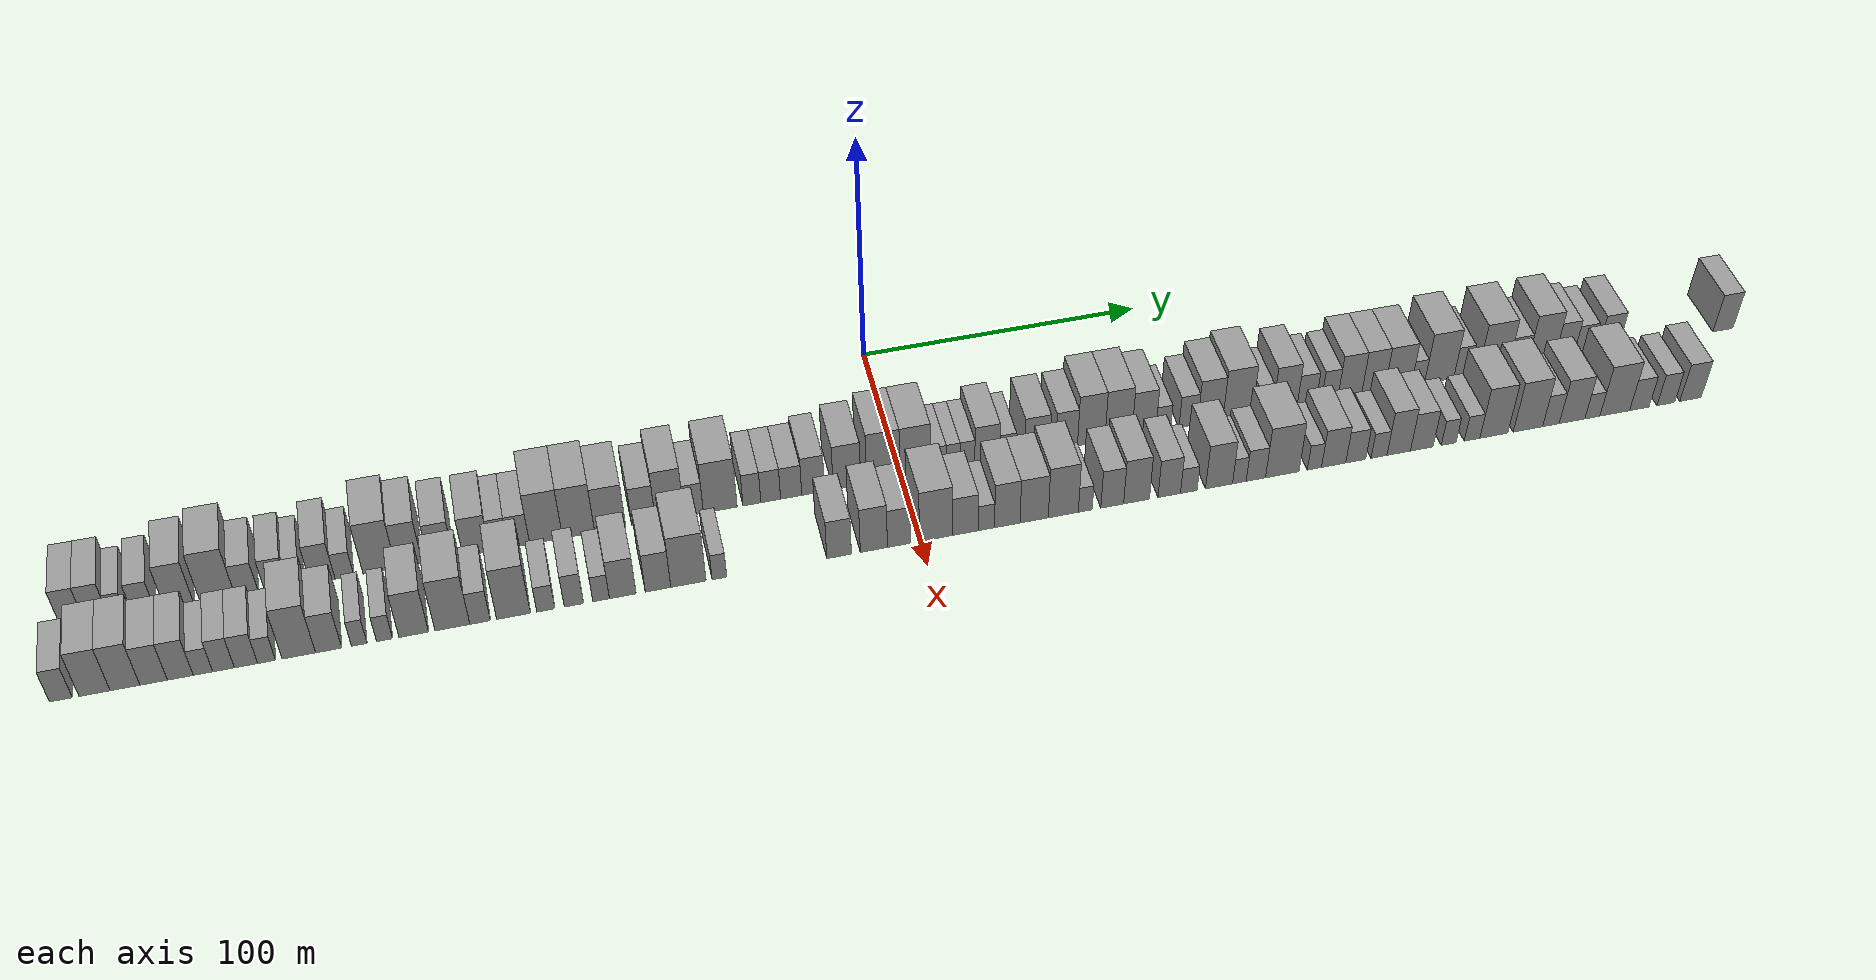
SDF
<sdf version="1.6">
 <world name="default">
  <scene>
   <sky><clouds><speed>12</speed></clouds></sky>
   <ambient>0.4 0.4 0.4 1</ambient>
   <background>0.7 0.7 0.7 1</background>
   <shadows>1</shadows>
  </scene>
  <gravity>0 0 -9.8066</gravity>
  <magnetic_field>6e-06 2.3e-05 -4.2e-05</magnetic_field>
  <physics default="0" name="default_physics" type="ode">
   <ode>
    <solver>
     <type>quick</type>
     <iters>10</iters>
     <sor>1.0</sor>
     <use_dynamic_moi_rescaling>0</use_dynamic_moi_rescaling>
    </solver>
    <constraints>
     <cfm>0</cfm>
     <erp>0.2</erp>
     <contact_max_correcting_vel>100</contact_max_correcting_vel>
     <contact_surface_layer>0.001</contact_surface_layer>
    </constraints>
   </ode>
   <max_step_size>0.004</max_step_size>
   <real_time_factor>1</real_time_factor>
   <real_time_update_rate>250</real_time_update_rate>
  </physics>
  <light name="sun" type="directional">
   <pose>0 0 10 0 0 0</pose>
   <diffuse>0.8 0.8 0.8 1</diffuse>
   <specular>0.2 0.2 0.2 1</specular>
   <attenuation>
    <range>1000</range>
    <constant>0.9</constant>
    <linear>0.01</linear>
    <quadratic>0.001</quadratic>
   </attenuation>
   <direction>-0.5 0.1 -0.9</direction>
  </light>
  <model name="building_1">
   <static>1</static>
   <pose>50.0000 -271.2881 0 0.000000 0.000000 0.000000</pose>
   <link name="link">
    <pose>0 0 9.00 0 0 0</pose>
    <collision name="collision"><geometry><box><size>20.0000 7.4239 18.0000</size></box></geometry></collision>
    <visual name="visual">
     <cast_shadows>0</cast_shadows>
     <geometry><box><size>20.0000 7.4239 18.0000</size></box></geometry>
     <material>
      <script>
       <uri>model://grey_wall/materials/scripts</uri>
       <uri>model://grey_wall/materials/textures</uri>
       <name>vrc/grey_wall</name>
      </script>
     </material>
    </visual>
   </link>
  </model>
  <model name="building_2">
   <static>1</static>
   <pose>50.0000 -263.7839 0 0.000000 0.000000 0.000000</pose>
   <link name="link">
    <pose>0 0 9.00 0 0 0</pose>
    <collision name="collision"><geometry><box><size>20.0000 7.5845 18.0000</size></box></geometry></collision>
    <visual name="visual">
     <cast_shadows>0</cast_shadows>
     <geometry><box><size>20.0000 7.5845 18.0000</size></box></geometry>
     <material>
      <script>
       <uri>model://grey_wall/materials/scripts</uri>
       <uri>model://grey_wall/materials/textures</uri>
       <name>vrc/grey_wall</name>
      </script>
     </material>
    </visual>
   </link>
  </model>
  <model name="building_3">
   <static>1</static>
   <pose>50.0000 -257.3614 0 0.000000 0.000000 0.000000</pose>
   <link name="link">
    <pose>0 0 6.00 0 0 0</pose>
    <collision name="collision"><geometry><box><size>20.0000 5.2606 12.0000</size></box></geometry></collision>
    <visual name="visual">
     <cast_shadows>0</cast_shadows>
     <geometry><box><size>20.0000 5.2606 12.0000</size></box></geometry>
     <material>
      <script>
       <uri>model://grey_wall/materials/scripts</uri>
       <uri>model://grey_wall/materials/textures</uri>
       <name>vrc/grey_wall</name>
      </script>
     </material>
    </visual>
   </link>
  </model>
  <model name="building_4">
   <static>1</static>
   <pose>50.0000 -249.2254 0 0.000000 0.000000 0.000000</pose>
   <link name="link">
    <pose>0 0 7.50 0 0 0</pose>
    <collision name="collision"><geometry><box><size>20.0000 7.0114 15.0000</size></box></geometry></collision>
    <visual name="visual">
     <cast_shadows>0</cast_shadows>
     <geometry><box><size>20.0000 7.0114 15.0000</size></box></geometry>
     <material>
      <script>
       <uri>model://grey_wall/materials/scripts</uri>
       <uri>model://grey_wall/materials/textures</uri>
       <name>vrc/grey_wall</name>
      </script>
     </material>
    </visual>
   </link>
  </model>
  <model name="building_5">
   <static>1</static>
   <pose>50.0000 -238.1553 0 0.000000 0.000000 0.000000</pose>
   <link name="link">
    <pose>0 0 10.50 0 0 0</pose>
    <collision name="collision"><geometry><box><size>20.0000 9.1288 21.0000</size></box></geometry></collision>
    <visual name="visual">
     <cast_shadows>0</cast_shadows>
     <geometry><box><size>20.0000 9.1288 21.0000</size></box></geometry>
     <material>
      <script>
       <uri>model://grey_wall/materials/scripts</uri>
       <uri>model://grey_wall/materials/textures</uri>
       <name>vrc/grey_wall</name>
      </script>
     </material>
    </visual>
   </link>
  </model>
  <model name="building_6">
   <static>1</static>
   <pose>50.0000 -226.0795 0 0.000000 0.000000 0.000000</pose>
   <link name="link">
    <pose>0 0 12.00 0 0 0</pose>
    <collision name="collision"><geometry><box><size>20.0000 11.0227 24.0000</size></box></geometry></collision>
    <visual name="visual">
     <cast_shadows>0</cast_shadows>
     <geometry><box><size>20.0000 11.0227 24.0000</size></box></geometry>
     <material>
      <script>
       <uri>model://grey_wall/materials/scripts</uri>
       <uri>model://grey_wall/materials/textures</uri>
       <name>vrc/grey_wall</name>
      </script>
     </material>
    </visual>
   </link>
  </model>
  <model name="building_7">
   <static>1</static>
   <pose>50.0000 -216.9120 0 0.000000 0.000000 0.000000</pose>
   <link name="link">
    <pose>0 0 7.50 0 0 0</pose>
    <collision name="collision"><geometry><box><size>20.0000 7.3123 15.0000</size></box></geometry></collision>
    <visual name="visual">
     <cast_shadows>0</cast_shadows>
     <geometry><box><size>20.0000 7.3123 15.0000</size></box></geometry>
     <material>
      <script>
       <uri>model://grey_wall/materials/scripts</uri>
       <uri>model://grey_wall/materials/textures</uri>
       <name>vrc/grey_wall</name>
      </script>
     </material>
    </visual>
   </link>
  </model>
  <model name="building_8">
   <static>1</static>
   <pose>50.0000 -207.6067 0 0.000000 0.000000 0.000000</pose>
   <link name="link">
    <pose>0 0 7.50 0 0 0</pose>
    <collision name="collision"><geometry><box><size>20.0000 7.2984 15.0000</size></box></geometry></collision>
    <visual name="visual">
     <cast_shadows>0</cast_shadows>
     <geometry><box><size>20.0000 7.2984 15.0000</size></box></geometry>
     <material>
      <script>
       <uri>model://grey_wall/materials/scripts</uri>
       <uri>model://grey_wall/materials/textures</uri>
       <name>vrc/grey_wall</name>
      </script>
     </material>
    </visual>
   </link>
  </model>
  <model name="building_9">
   <static>1</static>
   <pose>50.0000 -201.3462 0 0.000000 0.000000 0.000000</pose>
   <link name="link">
    <pose>0 0 6.00 0 0 0</pose>
    <collision name="collision"><geometry><box><size>20.0000 5.2227 12.0000</size></box></geometry></collision>
    <visual name="visual">
     <cast_shadows>0</cast_shadows>
     <geometry><box><size>20.0000 5.2227 12.0000</size></box></geometry>
     <material>
      <script>
       <uri>model://grey_wall/materials/scripts</uri>
       <uri>model://grey_wall/materials/textures</uri>
       <name>vrc/grey_wall</name>
      </script>
     </material>
    </visual>
   </link>
  </model>
  <model name="building_10">
   <static>1</static>
   <pose>50.0000 -192.7805 0 0.000000 0.000000 0.000000</pose>
   <link name="link">
    <pose>0 0 9.00 0 0 0</pose>
    <collision name="collision"><geometry><box><size>20.0000 7.9088 18.0000</size></box></geometry></collision>
    <visual name="visual">
     <cast_shadows>0</cast_shadows>
     <geometry><box><size>20.0000 7.9088 18.0000</size></box></geometry>
     <material>
      <script>
       <uri>model://grey_wall/materials/scripts</uri>
       <uri>model://grey_wall/materials/textures</uri>
       <name>vrc/grey_wall</name>
      </script>
     </material>
    </visual>
   </link>
  </model>
  <model name="building_11">
   <static>1</static>
   <pose>50.0000 -185.8272 0 0.000000 0.000000 0.000000</pose>
   <link name="link">
    <pose>0 0 6.00 0 0 0</pose>
    <collision name="collision"><geometry><box><size>20.0000 5.9977 12.0000</size></box></geometry></collision>
    <visual name="visual">
     <cast_shadows>0</cast_shadows>
     <geometry><box><size>20.0000 5.9977 12.0000</size></box></geometry>
     <material>
      <script>
       <uri>model://grey_wall/materials/scripts</uri>
       <uri>model://grey_wall/materials/textures</uri>
       <name>vrc/grey_wall</name>
      </script>
     </material>
    </visual>
   </link>
  </model>
  <model name="building_12">
   <static>1</static>
   <pose>50.0000 -174.4878 0 0.000000 0.000000 0.000000</pose>
   <link name="link">
    <pose>0 0 12.00 0 0 0</pose>
    <collision name="collision"><geometry><box><size>20.0000 10.6813 24.0000</size></box></geometry></collision>
    <visual name="visual">
     <cast_shadows>0</cast_shadows>
     <geometry><box><size>20.0000 10.6813 24.0000</size></box></geometry>
     <material>
      <script>
       <uri>model://grey_wall/materials/scripts</uri>
       <uri>model://grey_wall/materials/textures</uri>
       <name>vrc/grey_wall</name>
      </script>
     </material>
    </visual>
   </link>
  </model>
  <model name="building_13">
   <static>1</static>
   <pose>50.0000 -164.8769 0 0.000000 0.000000 0.000000</pose>
   <link name="link">
    <pose>0 0 10.50 0 0 0</pose>
    <collision name="collision"><geometry><box><size>20.0000 8.5405 21.0000</size></box></geometry></collision>
    <visual name="visual">
     <cast_shadows>0</cast_shadows>
     <geometry><box><size>20.0000 8.5405 21.0000</size></box></geometry>
     <material>
      <script>
       <uri>model://grey_wall/materials/scripts</uri>
       <uri>model://grey_wall/materials/textures</uri>
       <name>vrc/grey_wall</name>
      </script>
     </material>
    </visual>
   </link>
  </model>
  <model name="building_14">
   <static>1</static>
   <pose>50.0000 -154.5401 0 0.000000 0.000000 0.000000</pose>
   <link name="link">
    <pose>0 0 9.00 0 0 0</pose>
    <collision name="collision"><geometry><box><size>20.0000 8.1332 18.0000</size></box></geometry></collision>
    <visual name="visual">
     <cast_shadows>0</cast_shadows>
     <geometry><box><size>20.0000 8.1332 18.0000</size></box></geometry>
     <material>
      <script>
       <uri>model://grey_wall/materials/scripts</uri>
       <uri>model://grey_wall/materials/textures</uri>
       <name>vrc/grey_wall</name>
      </script>
     </material>
    </visual>
   </link>
  </model>
  <model name="building_15">
   <static>1</static>
   <pose>50.0000 -143.0563 0 0.000000 0.000000 0.000000</pose>
   <link name="link">
    <pose>0 0 9.00 0 0 0</pose>
    <collision name="collision"><geometry><box><size>20.0000 8.8343 18.0000</size></box></geometry></collision>
    <visual name="visual">
     <cast_shadows>0</cast_shadows>
     <geometry><box><size>20.0000 8.8343 18.0000</size></box></geometry>
     <material>
      <script>
       <uri>model://grey_wall/materials/scripts</uri>
       <uri>model://grey_wall/materials/textures</uri>
       <name>vrc/grey_wall</name>
      </script>
     </material>
    </visual>
   </link>
  </model>
  <model name="building_16">
   <static>1</static>
   <pose>50.0000 -135.6108 0 0.000000 0.000000 0.000000</pose>
   <link name="link">
    <pose>0 0 7.50 0 0 0</pose>
    <collision name="collision"><geometry><box><size>20.0000 6.0568 15.0000</size></box></geometry></collision>
    <visual name="visual">
     <cast_shadows>0</cast_shadows>
     <geometry><box><size>20.0000 6.0568 15.0000</size></box></geometry>
     <material>
      <script>
       <uri>model://grey_wall/materials/scripts</uri>
       <uri>model://grey_wall/materials/textures</uri>
       <name>vrc/grey_wall</name>
      </script>
     </material>
    </visual>
   </link>
  </model>
  <model name="building_17">
   <static>1</static>
   <pose>50.0000 -129.0847 0 0.000000 0.000000 0.000000</pose>
   <link name="link">
    <pose>0 0 7.50 0 0 0</pose>
    <collision name="collision"><geometry><box><size>20.0000 6.9954 15.0000</size></box></geometry></collision>
    <visual name="visual">
     <cast_shadows>0</cast_shadows>
     <geometry><box><size>20.0000 6.9954 15.0000</size></box></geometry>
     <material>
      <script>
       <uri>model://grey_wall/materials/scripts</uri>
       <uri>model://grey_wall/materials/textures</uri>
       <name>vrc/grey_wall</name>
      </script>
     </material>
    </visual>
   </link>
  </model>
  <model name="building_18">
   <static>1</static>
   <pose>50.0000 -120.1459 0 0.000000 0.000000 0.000000</pose>
   <link name="link">
    <pose>0 0 12.00 0 0 0</pose>
    <collision name="collision"><geometry><box><size>20.0000 10.8822 24.0000</size></box></geometry></collision>
    <visual name="visual">
     <cast_shadows>0</cast_shadows>
     <geometry><box><size>20.0000 10.8822 24.0000</size></box></geometry>
     <material>
      <script>
       <uri>model://grey_wall/materials/scripts</uri>
       <uri>model://grey_wall/materials/textures</uri>
       <name>vrc/grey_wall</name>
      </script>
     </material>
    </visual>
   </link>
  </model>
  <model name="building_19">
   <static>1</static>
   <pose>50.0000 -109.3991 0 0.000000 0.000000 0.000000</pose>
   <link name="link">
    <pose>0 0 12.00 0 0 0</pose>
    <collision name="collision"><geometry><box><size>20.0000 10.6114 24.0000</size></box></geometry></collision>
    <visual name="visual">
     <cast_shadows>0</cast_shadows>
     <geometry><box><size>20.0000 10.6114 24.0000</size></box></geometry>
     <material>
      <script>
       <uri>model://grey_wall/materials/scripts</uri>
       <uri>model://grey_wall/materials/textures</uri>
       <name>vrc/grey_wall</name>
      </script>
     </material>
    </visual>
   </link>
  </model>
  <model name="building_20">
   <static>1</static>
   <pose>50.0000 -98.9195 0 0.000000 0.000000 0.000000</pose>
   <link name="link">
    <pose>0 0 10.50 0 0 0</pose>
    <collision name="collision"><geometry><box><size>20.0000 10.3479 21.0000</size></box></geometry></collision>
    <visual name="visual">
     <cast_shadows>0</cast_shadows>
     <geometry><box><size>20.0000 10.3479 21.0000</size></box></geometry>
     <material>
      <script>
       <uri>model://grey_wall/materials/scripts</uri>
       <uri>model://grey_wall/materials/textures</uri>
       <name>vrc/grey_wall</name>
      </script>
     </material>
    </visual>
   </link>
  </model>
  <model name="building_21">
   <static>1</static>
   <pose>50.0000 -87.7739 0 0.000000 0.000000 0.000000</pose>
   <link name="link">
    <pose>0 0 9.00 0 0 0</pose>
    <collision name="collision"><geometry><box><size>20.0000 7.9433 18.0000</size></box></geometry></collision>
    <visual name="visual">
     <cast_shadows>0</cast_shadows>
     <geometry><box><size>20.0000 7.9433 18.0000</size></box></geometry>
     <material>
      <script>
       <uri>model://grey_wall/materials/scripts</uri>
       <uri>model://grey_wall/materials/textures</uri>
       <name>vrc/grey_wall</name>
      </script>
     </material>
    </visual>
   </link>
  </model>
  <model name="building_22">
   <static>1</static>
   <pose>50.0000 -78.9859 0 0.000000 0.000000 0.000000</pose>
   <link name="link">
    <pose>0 0 12.00 0 0 0</pose>
    <collision name="collision"><geometry><box><size>20.0000 9.6326 24.0000</size></box></geometry></collision>
    <visual name="visual">
     <cast_shadows>0</cast_shadows>
     <geometry><box><size>20.0000 9.6326 24.0000</size></box></geometry>
     <material>
      <script>
       <uri>model://grey_wall/materials/scripts</uri>
       <uri>model://grey_wall/materials/textures</uri>
       <name>vrc/grey_wall</name>
      </script>
     </material>
    </visual>
   </link>
  </model>
  <model name="building_23">
   <static>1</static>
   <pose>50.0000 -70.9266 0 0.000000 0.000000 0.000000</pose>
   <link name="link">
    <pose>0 0 7.50 0 0 0</pose>
    <collision name="collision"><geometry><box><size>20.0000 6.4860 15.0000</size></box></geometry></collision>
    <visual name="visual">
     <cast_shadows>0</cast_shadows>
     <geometry><box><size>20.0000 6.4860 15.0000</size></box></geometry>
     <material>
      <script>
       <uri>model://grey_wall/materials/scripts</uri>
       <uri>model://grey_wall/materials/textures</uri>
       <name>vrc/grey_wall</name>
      </script>
     </material>
    </visual>
   </link>
  </model>
  <model name="building_24">
   <static>1</static>
   <pose>50.0000 -61.9832 0 0.000000 0.000000 0.000000</pose>
   <link name="link">
    <pose>0 0 12.00 0 0 0</pose>
    <collision name="collision"><geometry><box><size>20.0000 11.4007 24.0000</size></box></geometry></collision>
    <visual name="visual">
     <cast_shadows>0</cast_shadows>
     <geometry><box><size>20.0000 11.4007 24.0000</size></box></geometry>
     <material>
      <script>
       <uri>model://grey_wall/materials/scripts</uri>
       <uri>model://grey_wall/materials/textures</uri>
       <name>vrc/grey_wall</name>
      </script>
     </material>
    </visual>
   </link>
  </model>
  <model name="building_25">
   <static>1</static>
   <pose>50.0000 -51.2385 0 0.000000 0.000000 0.000000</pose>
   <link name="link">
    <pose>0 0 7.50 0 0 0</pose>
    <collision name="collision"><geometry><box><size>20.0000 6.0887 15.0000</size></box></geometry></collision>
    <visual name="visual">
     <cast_shadows>0</cast_shadows>
     <geometry><box><size>20.0000 6.0887 15.0000</size></box></geometry>
     <material>
      <script>
       <uri>model://grey_wall/materials/scripts</uri>
       <uri>model://grey_wall/materials/textures</uri>
       <name>vrc/grey_wall</name>
      </script>
     </material>
    </visual>
   </link>
  </model>
  <model name="building_26">
   <static>1</static>
   <pose>50.0000 -44.8371 0 0.000000 0.000000 0.000000</pose>
   <link name="link">
    <pose>0 0 7.50 0 0 0</pose>
    <collision name="collision"><geometry><box><size>20.0000 6.7143 15.0000</size></box></geometry></collision>
    <visual name="visual">
     <cast_shadows>0</cast_shadows>
     <geometry><box><size>20.0000 6.7143 15.0000</size></box></geometry>
     <material>
      <script>
       <uri>model://grey_wall/materials/scripts</uri>
       <uri>model://grey_wall/materials/textures</uri>
       <name>vrc/grey_wall</name>
      </script>
     </material>
    </visual>
   </link>
  </model>
  <model name="building_27">
   <static>1</static>
   <pose>50.0000 -37.8603 0 0.000000 0.000000 0.000000</pose>
   <link name="link">
    <pose>0 0 7.50 0 0 0</pose>
    <collision name="collision"><geometry><box><size>20.0000 7.2393 15.0000</size></box></geometry></collision>
    <visual name="visual">
     <cast_shadows>0</cast_shadows>
     <geometry><box><size>20.0000 7.2393 15.0000</size></box></geometry>
     <material>
      <script>
       <uri>model://grey_wall/materials/scripts</uri>
       <uri>model://grey_wall/materials/textures</uri>
       <name>vrc/grey_wall</name>
      </script>
     </material>
    </visual>
   </link>
  </model>
  <model name="building_28">
   <static>1</static>
   <pose>50.0000 -30.3558 0 0.000000 0.000000 0.000000</pose>
   <link name="link">
    <pose>0 0 9.00 0 0 0</pose>
    <collision name="collision"><geometry><box><size>20.0000 7.7696 18.0000</size></box></geometry></collision>
    <visual name="visual">
     <cast_shadows>0</cast_shadows>
     <geometry><box><size>20.0000 7.7696 18.0000</size></box></geometry>
     <material>
      <script>
       <uri>model://grey_wall/materials/scripts</uri>
       <uri>model://grey_wall/materials/textures</uri>
       <name>vrc/grey_wall</name>
      </script>
     </material>
    </visual>
   </link>
  </model>
  <model name="building_29">
   <static>1</static>
   <pose>50.0000 -18.7199 0 0.000000 0.000000 0.000000</pose>
   <link name="link">
    <pose>0 0 10.50 0 0 0</pose>
    <collision name="collision"><geometry><box><size>20.0000 9.5024 21.0000</size></box></geometry></collision>
    <visual name="visual">
     <cast_shadows>0</cast_shadows>
     <geometry><box><size>20.0000 9.5024 21.0000</size></box></geometry>
     <material>
      <script>
       <uri>model://grey_wall/materials/scripts</uri>
       <uri>model://grey_wall/materials/textures</uri>
       <name>vrc/grey_wall</name>
      </script>
     </material>
    </visual>
   </link>
  </model>
  <model name="building_30">
   <static>1</static>
   <pose>50.0000 -6.2122 0 0.000000 0.000000 0.000000</pose>
   <link name="link">
    <pose>0 0 12.00 0 0 0</pose>
    <collision name="collision"><geometry><box><size>20.0000 11.5130 24.0000</size></box></geometry></collision>
    <visual name="visual">
     <cast_shadows>0</cast_shadows>
     <geometry><box><size>20.0000 11.5130 24.0000</size></box></geometry>
     <material>
      <script>
       <uri>model://grey_wall/materials/scripts</uri>
       <uri>model://grey_wall/materials/textures</uri>
       <name>vrc/grey_wall</name>
      </script>
     </material>
    </visual>
   </link>
  </model>
  <model name="building_31">
   <static>1</static>
   <pose>50.0000 4.8688 0 0.000000 0.000000 0.000000</pose>
   <link name="link">
    <pose>0 0 12.00 0 0 0</pose>
    <collision name="collision"><geometry><box><size>20.0000 10.6490 24.0000</size></box></geometry></collision>
    <visual name="visual">
     <cast_shadows>0</cast_shadows>
     <geometry><box><size>20.0000 10.6490 24.0000</size></box></geometry>
     <material>
      <script>
       <uri>model://grey_wall/materials/scripts</uri>
       <uri>model://grey_wall/materials/textures</uri>
       <name>vrc/grey_wall</name>
      </script>
     </material>
    </visual>
   </link>
  </model>
  <model name="building_32">
   <static>1</static>
   <pose>50.0000 12.9377 0 0.000000 0.000000 0.000000</pose>
   <link name="link">
    <pose>0 0 6.00 0 0 0</pose>
    <collision name="collision"><geometry><box><size>20.0000 5.4888 12.0000</size></box></geometry></collision>
    <visual name="visual">
     <cast_shadows>0</cast_shadows>
     <geometry><box><size>20.0000 5.4888 12.0000</size></box></geometry>
     <material>
      <script>
       <uri>model://grey_wall/materials/scripts</uri>
       <uri>model://grey_wall/materials/textures</uri>
       <name>vrc/grey_wall</name>
      </script>
     </material>
    </visual>
   </link>
  </model>
  <model name="building_33">
   <static>1</static>
   <pose>50.0000 18.0976 0 0.000000 0.000000 0.000000</pose>
   <link name="link">
    <pose>0 0 6.00 0 0 0</pose>
    <collision name="collision"><geometry><box><size>20.0000 4.8309 12.0000</size></box></geometry></collision>
    <visual name="visual">
     <cast_shadows>0</cast_shadows>
     <geometry><box><size>20.0000 4.8309 12.0000</size></box></geometry>
     <material>
      <script>
       <uri>model://grey_wall/materials/scripts</uri>
       <uri>model://grey_wall/materials/textures</uri>
       <name>vrc/grey_wall</name>
      </script>
     </material>
    </visual>
   </link>
  </model>
  <model name="building_34">
   <static>1</static>
   <pose>50.0000 23.0906 0 0.000000 0.000000 0.000000</pose>
   <link name="link">
    <pose>0 0 6.00 0 0 0</pose>
    <collision name="collision"><geometry><box><size>20.0000 5.1552 12.0000</size></box></geometry></collision>
    <visual name="visual">
     <cast_shadows>0</cast_shadows>
     <geometry><box><size>20.0000 5.1552 12.0000</size></box></geometry>
     <material>
      <script>
       <uri>model://grey_wall/materials/scripts</uri>
       <uri>model://grey_wall/materials/textures</uri>
       <name>vrc/grey_wall</name>
      </script>
     </material>
    </visual>
   </link>
  </model>
  <model name="building_35">
   <static>1</static>
   <pose>50.0000 30.0514 0 0.000000 0.000000 0.000000</pose>
   <link name="link">
    <pose>0 0 9.00 0 0 0</pose>
    <collision name="collision"><geometry><box><size>20.0000 8.7663 18.0000</size></box></geometry></collision>
    <visual name="visual">
     <cast_shadows>0</cast_shadows>
     <geometry><box><size>20.0000 8.7663 18.0000</size></box></geometry>
     <material>
      <script>
       <uri>model://grey_wall/materials/scripts</uri>
       <uri>model://grey_wall/materials/textures</uri>
       <name>vrc/grey_wall</name>
      </script>
     </material>
    </visual>
   </link>
  </model>
  <model name="building_36">
   <static>1</static>
   <pose>50.0000 37.3147 0 0.000000 0.000000 0.000000</pose>
   <link name="link">
    <pose>0 0 6.00 0 0 0</pose>
    <collision name="collision"><geometry><box><size>20.0000 5.7603 12.0000</size></box></geometry></collision>
    <visual name="visual">
     <cast_shadows>0</cast_shadows>
     <geometry><box><size>20.0000 5.7603 12.0000</size></box></geometry>
     <material>
      <script>
       <uri>model://grey_wall/materials/scripts</uri>
       <uri>model://grey_wall/materials/textures</uri>
       <name>vrc/grey_wall</name>
      </script>
     </material>
    </visual>
   </link>
  </model>
  <model name="building_37">
   <static>1</static>
   <pose>50.0000 47.6836 0 0.000000 0.000000 0.000000</pose>
   <link name="link">
    <pose>0 0 9.00 0 0 0</pose>
    <collision name="collision"><geometry><box><size>20.0000 8.9776 18.0000</size></box></geometry></collision>
    <visual name="visual">
     <cast_shadows>0</cast_shadows>
     <geometry><box><size>20.0000 8.9776 18.0000</size></box></geometry>
     <material>
      <script>
       <uri>model://grey_wall/materials/scripts</uri>
       <uri>model://grey_wall/materials/textures</uri>
       <name>vrc/grey_wall</name>
      </script>
     </material>
    </visual>
   </link>
  </model>
  <model name="building_38">
   <static>1</static>
   <pose>50.0000 58.0667 0 0.000000 0.000000 0.000000</pose>
   <link name="link">
    <pose>0 0 9.00 0 0 0</pose>
    <collision name="collision"><geometry><box><size>20.0000 7.7886 18.0000</size></box></geometry></collision>
    <visual name="visual">
     <cast_shadows>0</cast_shadows>
     <geometry><box><size>20.0000 7.7886 18.0000</size></box></geometry>
     <material>
      <script>
       <uri>model://grey_wall/materials/scripts</uri>
       <uri>model://grey_wall/materials/textures</uri>
       <name>vrc/grey_wall</name>
      </script>
     </material>
    </visual>
   </link>
  </model>
  <model name="building_39">
   <static>1</static>
   <pose>50.0000 66.8419 0 0.000000 0.000000 0.000000</pose>
   <link name="link">
    <pose>0 0 12.00 0 0 0</pose>
    <collision name="collision"><geometry><box><size>20.0000 9.7617 24.0000</size></box></geometry></collision>
    <visual name="visual">
     <cast_shadows>0</cast_shadows>
     <geometry><box><size>20.0000 9.7617 24.0000</size></box></geometry>
     <material>
      <script>
       <uri>model://grey_wall/materials/scripts</uri>
       <uri>model://grey_wall/materials/textures</uri>
       <name>vrc/grey_wall</name>
      </script>
     </material>
    </visual>
   </link>
  </model>
  <model name="building_40">
   <static>1</static>
   <pose>50.0000 76.5627 0 0.000000 0.000000 0.000000</pose>
   <link name="link">
    <pose>0 0 12.00 0 0 0</pose>
    <collision name="collision"><geometry><box><size>20.0000 9.6800 24.0000</size></box></geometry></collision>
    <visual name="visual">
     <cast_shadows>0</cast_shadows>
     <geometry><box><size>20.0000 9.6800 24.0000</size></box></geometry>
     <material>
      <script>
       <uri>model://grey_wall/materials/scripts</uri>
       <uri>model://grey_wall/materials/textures</uri>
       <name>vrc/grey_wall</name>
      </script>
     </material>
    </visual>
   </link>
  </model>
  <model name="building_41">
   <static>1</static>
   <pose>50.0000 85.6968 0 0.000000 0.000000 0.000000</pose>
   <link name="link">
    <pose>0 0 10.50 0 0 0</pose>
    <collision name="collision"><geometry><box><size>20.0000 8.5882 21.0000</size></box></geometry></collision>
    <visual name="visual">
     <cast_shadows>0</cast_shadows>
     <geometry><box><size>20.0000 8.5882 21.0000</size></box></geometry>
     <material>
      <script>
       <uri>model://grey_wall/materials/scripts</uri>
       <uri>model://grey_wall/materials/textures</uri>
       <name>vrc/grey_wall</name>
      </script>
     </material>
    </visual>
   </link>
  </model>
  <model name="building_42">
   <static>1</static>
   <pose>50.0000 92.6843 0 0.000000 0.000000 0.000000</pose>
   <link name="link">
    <pose>0 0 6.00 0 0 0</pose>
    <collision name="collision"><geometry><box><size>20.0000 5.3866 12.0000</size></box></geometry></collision>
    <visual name="visual">
     <cast_shadows>0</cast_shadows>
     <geometry><box><size>20.0000 5.3866 12.0000</size></box></geometry>
     <material>
      <script>
       <uri>model://grey_wall/materials/scripts</uri>
       <uri>model://grey_wall/materials/textures</uri>
       <name>vrc/grey_wall</name>
      </script>
     </material>
    </visual>
   </link>
  </model>
  <model name="building_43">
   <static>1</static>
   <pose>50.0000 101.7371 0 0.000000 0.000000 0.000000</pose>
   <link name="link">
    <pose>0 0 7.50 0 0 0</pose>
    <collision name="collision"><geometry><box><size>20.0000 6.7191 15.0000</size></box></geometry></collision>
    <visual name="visual">
     <cast_shadows>0</cast_shadows>
     <geometry><box><size>20.0000 6.7191 15.0000</size></box></geometry>
     <material>
      <script>
       <uri>model://grey_wall/materials/scripts</uri>
       <uri>model://grey_wall/materials/textures</uri>
       <name>vrc/grey_wall</name>
      </script>
     </material>
    </visual>
   </link>
  </model>
  <model name="building_44">
   <static>1</static>
   <pose>50.0000 109.6853 0 0.000000 0.000000 0.000000</pose>
   <link name="link">
    <pose>0 0 10.50 0 0 0</pose>
    <collision name="collision"><geometry><box><size>20.0000 9.1772 21.0000</size></box></geometry></collision>
    <visual name="visual">
     <cast_shadows>0</cast_shadows>
     <geometry><box><size>20.0000 9.1772 21.0000</size></box></geometry>
     <material>
      <script>
       <uri>model://grey_wall/materials/scripts</uri>
       <uri>model://grey_wall/materials/textures</uri>
       <name>vrc/grey_wall</name>
      </script>
     </material>
    </visual>
   </link>
  </model>
  <model name="building_45">
   <static>1</static>
   <pose>50.0000 119.6319 0 0.000000 0.000000 0.000000</pose>
   <link name="link">
    <pose>0 0 12.00 0 0 0</pose>
    <collision name="collision"><geometry><box><size>20.0000 10.7161 24.0000</size></box></geometry></collision>
    <visual name="visual">
     <cast_shadows>0</cast_shadows>
     <geometry><box><size>20.0000 10.7161 24.0000</size></box></geometry>
     <material>
      <script>
       <uri>model://grey_wall/materials/scripts</uri>
       <uri>model://grey_wall/materials/textures</uri>
       <name>vrc/grey_wall</name>
      </script>
     </material>
    </visual>
   </link>
  </model>
  <model name="building_46">
   <static>1</static>
   <pose>50.0000 129.7484 0 0.000000 0.000000 0.000000</pose>
   <link name="link">
    <pose>0 0 6.00 0 0 0</pose>
    <collision name="collision"><geometry><box><size>20.0000 5.5169 12.0000</size></box></geometry></collision>
    <visual name="visual">
     <cast_shadows>0</cast_shadows>
     <geometry><box><size>20.0000 5.5169 12.0000</size></box></geometry>
     <material>
      <script>
       <uri>model://grey_wall/materials/scripts</uri>
       <uri>model://grey_wall/materials/textures</uri>
       <name>vrc/grey_wall</name>
      </script>
     </material>
    </visual>
   </link>
  </model>
  <model name="building_47">
   <static>1</static>
   <pose>50.0000 136.9675 0 0.000000 0.000000 0.000000</pose>
   <link name="link">
    <pose>0 0 10.50 0 0 0</pose>
    <collision name="collision"><geometry><box><size>20.0000 8.9213 21.0000</size></box></geometry></collision>
    <visual name="visual">
     <cast_shadows>0</cast_shadows>
     <geometry><box><size>20.0000 8.9213 21.0000</size></box></geometry>
     <material>
      <script>
       <uri>model://grey_wall/materials/scripts</uri>
       <uri>model://grey_wall/materials/textures</uri>
       <name>vrc/grey_wall</name>
      </script>
     </material>
    </visual>
   </link>
  </model>
  <model name="building_48">
   <static>1</static>
   <pose>50.0000 144.8917 0 0.000000 0.000000 0.000000</pose>
   <link name="link">
    <pose>0 0 7.50 0 0 0</pose>
    <collision name="collision"><geometry><box><size>20.0000 6.9271 15.0000</size></box></geometry></collision>
    <visual name="visual">
     <cast_shadows>0</cast_shadows>
     <geometry><box><size>20.0000 6.9271 15.0000</size></box></geometry>
     <material>
      <script>
       <uri>model://grey_wall/materials/scripts</uri>
       <uri>model://grey_wall/materials/textures</uri>
       <name>vrc/grey_wall</name>
      </script>
     </material>
    </visual>
   </link>
  </model>
  <model name="building_49">
   <static>1</static>
   <pose>50.0000 153.3730 0 0.000000 0.000000 0.000000</pose>
   <link name="link">
    <pose>0 0 7.50 0 0 0</pose>
    <collision name="collision"><geometry><box><size>20.0000 6.0354 15.0000</size></box></geometry></collision>
    <visual name="visual">
     <cast_shadows>0</cast_shadows>
     <geometry><box><size>20.0000 6.0354 15.0000</size></box></geometry>
     <material>
      <script>
       <uri>model://grey_wall/materials/scripts</uri>
       <uri>model://grey_wall/materials/textures</uri>
       <name>vrc/grey_wall</name>
      </script>
     </material>
    </visual>
   </link>
  </model>
  <model name="building_50">
   <static>1</static>
   <pose>50.0000 160.8095 0 0.000000 0.000000 0.000000</pose>
   <link name="link">
    <pose>0 0 10.50 0 0 0</pose>
    <collision name="collision"><geometry><box><size>20.0000 8.8377 21.0000</size></box></geometry></collision>
    <visual name="visual">
     <cast_shadows>0</cast_shadows>
     <geometry><box><size>20.0000 8.8377 21.0000</size></box></geometry>
     <material>
      <script>
       <uri>model://grey_wall/materials/scripts</uri>
       <uri>model://grey_wall/materials/textures</uri>
       <name>vrc/grey_wall</name>
      </script>
     </material>
    </visual>
   </link>
  </model>
  <model name="building_51">
   <static>1</static>
   <pose>50.0000 169.5152 0 0.000000 0.000000 0.000000</pose>
   <link name="link">
    <pose>0 0 10.50 0 0 0</pose>
    <collision name="collision"><geometry><box><size>20.0000 8.5737 21.0000</size></box></geometry></collision>
    <visual name="visual">
     <cast_shadows>0</cast_shadows>
     <geometry><box><size>20.0000 8.5737 21.0000</size></box></geometry>
     <material>
      <script>
       <uri>model://grey_wall/materials/scripts</uri>
       <uri>model://grey_wall/materials/textures</uri>
       <name>vrc/grey_wall</name>
      </script>
     </material>
    </visual>
   </link>
  </model>
  <model name="building_52">
   <static>1</static>
   <pose>50.0000 178.7952 0 0.000000 0.000000 0.000000</pose>
   <link name="link">
    <pose>0 0 10.50 0 0 0</pose>
    <collision name="collision"><geometry><box><size>20.0000 9.9862 21.0000</size></box></geometry></collision>
    <visual name="visual">
     <cast_shadows>0</cast_shadows>
     <geometry><box><size>20.0000 9.9862 21.0000</size></box></geometry>
     <material>
      <script>
       <uri>model://grey_wall/materials/scripts</uri>
       <uri>model://grey_wall/materials/textures</uri>
       <name>vrc/grey_wall</name>
      </script>
     </material>
    </visual>
   </link>
  </model>
  <model name="building_53">
   <static>1</static>
   <pose>50.0000 186.2557 0 0.000000 0.000000 0.000000</pose>
   <link name="link">
    <pose>0 0 6.00 0 0 0</pose>
    <collision name="collision"><geometry><box><size>20.0000 4.9349 12.0000</size></box></geometry></collision>
    <visual name="visual">
     <cast_shadows>0</cast_shadows>
     <geometry><box><size>20.0000 4.9349 12.0000</size></box></geometry>
     <material>
      <script>
       <uri>model://grey_wall/materials/scripts</uri>
       <uri>model://grey_wall/materials/textures</uri>
       <name>vrc/grey_wall</name>
      </script>
     </material>
    </visual>
   </link>
  </model>
  <model name="building_54">
   <static>1</static>
   <pose>50.0000 194.2151 0 0.000000 0.000000 0.000000</pose>
   <link name="link">
    <pose>0 0 12.00 0 0 0</pose>
    <collision name="collision"><geometry><box><size>20.0000 10.9838 24.0000</size></box></geometry></collision>
    <visual name="visual">
     <cast_shadows>0</cast_shadows>
     <geometry><box><size>20.0000 10.9838 24.0000</size></box></geometry>
     <material>
      <script>
       <uri>model://grey_wall/materials/scripts</uri>
       <uri>model://grey_wall/materials/textures</uri>
       <name>vrc/grey_wall</name>
      </script>
     </material>
    </visual>
   </link>
  </model>
  <model name="building_55">
   <static>1</static>
   <pose>50.0000 202.7680 0 0.000000 0.000000 0.000000</pose>
   <link name="link">
    <pose>0 0 7.50 0 0 0</pose>
    <collision name="collision"><geometry><box><size>20.0000 6.1220 15.0000</size></box></geometry></collision>
    <visual name="visual">
     <cast_shadows>0</cast_shadows>
     <geometry><box><size>20.0000 6.1220 15.0000</size></box></geometry>
     <material>
      <script>
       <uri>model://grey_wall/materials/scripts</uri>
       <uri>model://grey_wall/materials/textures</uri>
       <name>vrc/grey_wall</name>
      </script>
     </material>
    </visual>
   </link>
  </model>
  <model name="building_56">
   <static>1</static>
   <pose>50.0000 214.5479 0 0.000000 0.000000 0.000000</pose>
   <link name="link">
    <pose>0 0 12.00 0 0 0</pose>
    <collision name="collision"><geometry><box><size>20.0000 11.4379 24.0000</size></box></geometry></collision>
    <visual name="visual">
     <cast_shadows>0</cast_shadows>
     <geometry><box><size>20.0000 11.4379 24.0000</size></box></geometry>
     <material>
      <script>
       <uri>model://grey_wall/materials/scripts</uri>
       <uri>model://grey_wall/materials/textures</uri>
       <name>vrc/grey_wall</name>
      </script>
     </material>
    </visual>
   </link>
  </model>
  <model name="building_57">
   <static>1</static>
   <pose>50.0000 223.8794 0 0.000000 0.000000 0.000000</pose>
   <link name="link">
    <pose>0 0 7.50 0 0 0</pose>
    <collision name="collision"><geometry><box><size>20.0000 7.2250 15.0000</size></box></geometry></collision>
    <visual name="visual">
     <cast_shadows>0</cast_shadows>
     <geometry><box><size>20.0000 7.2250 15.0000</size></box></geometry>
     <material>
      <script>
       <uri>model://grey_wall/materials/scripts</uri>
       <uri>model://grey_wall/materials/textures</uri>
       <name>vrc/grey_wall</name>
      </script>
     </material>
    </visual>
   </link>
  </model>
  <model name="building_58">
   <static>1</static>
   <pose>50.0000 232.6430 0 0.000000 0.000000 0.000000</pose>
   <link name="link">
    <pose>0 0 12.00 0 0 0</pose>
    <collision name="collision"><geometry><box><size>20.0000 10.3021 24.0000</size></box></geometry></collision>
    <visual name="visual">
     <cast_shadows>0</cast_shadows>
     <geometry><box><size>20.0000 10.3021 24.0000</size></box></geometry>
     <material>
      <script>
       <uri>model://grey_wall/materials/scripts</uri>
       <uri>model://grey_wall/materials/textures</uri>
       <name>vrc/grey_wall</name>
      </script>
     </material>
    </visual>
   </link>
  </model>
  <model name="building_59">
   <static>1</static>
   <pose>50.0000 241.4697 0 0.000000 0.000000 0.000000</pose>
   <link name="link">
    <pose>0 0 9.00 0 0 0</pose>
    <collision name="collision"><geometry><box><size>20.0000 7.3514 18.0000</size></box></geometry></collision>
    <visual name="visual">
     <cast_shadows>0</cast_shadows>
     <geometry><box><size>20.0000 7.3514 18.0000</size></box></geometry>
     <material>
      <script>
       <uri>model://grey_wall/materials/scripts</uri>
       <uri>model://grey_wall/materials/textures</uri>
       <name>vrc/grey_wall</name>
      </script>
     </material>
    </visual>
   </link>
  </model>
  <model name="building_60">
   <static>1</static>
   <pose>50.0000 248.7825 0 0.000000 0.000000 0.000000</pose>
   <link name="link">
    <pose>0 0 7.50 0 0 0</pose>
    <collision name="collision"><geometry><box><size>20.0000 7.2742 15.0000</size></box></geometry></collision>
    <visual name="visual">
     <cast_shadows>0</cast_shadows>
     <geometry><box><size>20.0000 7.2742 15.0000</size></box></geometry>
     <material>
      <script>
       <uri>model://grey_wall/materials/scripts</uri>
       <uri>model://grey_wall/materials/textures</uri>
       <name>vrc/grey_wall</name>
      </script>
     </material>
    </visual>
   </link>
  </model>
  <model name="building_61">
   <static>1</static>
   <pose>50.0000 258.3505 0 0.000000 0.000000 0.000000</pose>
   <link name="link">
    <pose>0 0 9.00 0 0 0</pose>
    <collision name="collision"><geometry><box><size>20.0000 7.8619 18.0000</size></box></geometry></collision>
    <visual name="visual">
     <cast_shadows>0</cast_shadows>
     <geometry><box><size>20.0000 7.8619 18.0000</size></box></geometry>
     <material>
      <script>
       <uri>model://grey_wall/materials/scripts</uri>
       <uri>model://grey_wall/materials/textures</uri>
       <name>vrc/grey_wall</name>
      </script>
     </material>
    </visual>
   </link>
  </model>
  <model name="building_62">
   <static>1</static>
   <pose>50.0000 303.1234 0 0.000000 0.000000 0.000000</pose>
   <link name="link">
    <pose>0 0 9.00 0 0 0</pose>
    <collision name="collision"><geometry><box><size>20.0000 7.8946 18.0000</size></box></geometry></collision>
    <visual name="visual">
     <cast_shadows>0</cast_shadows>
     <geometry><box><size>20.0000 7.8946 18.0000</size></box></geometry>
     <material>
      <script>
       <uri>model://grey_wall/materials/scripts</uri>
       <uri>model://grey_wall/materials/textures</uri>
       <name>vrc/grey_wall</name>
      </script>
     </material>
    </visual>
   </link>
  </model>
  <model name="building_63">
   <static>1</static>
   <pose>79.0000 -274.5551 0 0.000000 0.000000 0.000000</pose>
   <link name="link">
    <pose>0 0 7.50 0 0 0</pose>
    <collision name="collision"><geometry><box><size>20.0000 6.8898 15.0000</size></box></geometry></collision>
    <visual name="visual">
     <cast_shadows>0</cast_shadows>
     <geometry><box><size>20.0000 6.8898 15.0000</size></box></geometry>
     <material>
      <script>
       <uri>model://grey_wall/materials/scripts</uri>
       <uri>model://grey_wall/materials/textures</uri>
       <name>vrc/grey_wall</name>
      </script>
     </material>
    </visual>
   </link>
  </model>
  <model name="building_64">
   <static>1</static>
   <pose>79.0000 -264.4121 0 0.000000 0.000000 0.000000</pose>
   <link name="link">
    <pose>0 0 10.50 0 0 0</pose>
    <collision name="collision"><geometry><box><size>20.0000 9.3963 21.0000</size></box></geometry></collision>
    <visual name="visual">
     <cast_shadows>0</cast_shadows>
     <geometry><box><size>20.0000 9.3963 21.0000</size></box></geometry>
     <material>
      <script>
       <uri>model://grey_wall/materials/scripts</uri>
       <uri>model://grey_wall/materials/textures</uri>
       <name>vrc/grey_wall</name>
      </script>
     </material>
    </visual>
   </link>
  </model>
  <model name="building_65">
   <static>1</static>
   <pose>79.0000 -255.1924 0 0.000000 0.000000 0.000000</pose>
   <link name="link">
    <pose>0 0 10.50 0 0 0</pose>
    <collision name="collision"><geometry><box><size>20.0000 9.0431 21.0000</size></box></geometry></collision>
    <visual name="visual">
     <cast_shadows>0</cast_shadows>
     <geometry><box><size>20.0000 9.0431 21.0000</size></box></geometry>
     <material>
      <script>
       <uri>model://grey_wall/materials/scripts</uri>
       <uri>model://grey_wall/materials/textures</uri>
       <name>vrc/grey_wall</name>
      </script>
     </material>
    </visual>
   </link>
  </model>
  <model name="building_66">
   <static>1</static>
   <pose>79.0000 -246.4859 0 0.000000 0.000000 0.000000</pose>
   <link name="link">
    <pose>0 0 9.00 0 0 0</pose>
    <collision name="collision"><geometry><box><size>20.0000 8.3699 18.0000</size></box></geometry></collision>
    <visual name="visual">
     <cast_shadows>0</cast_shadows>
     <geometry><box><size>20.0000 8.3699 18.0000</size></box></geometry>
     <material>
      <script>
       <uri>model://grey_wall/materials/scripts</uri>
       <uri>model://grey_wall/materials/textures</uri>
       <name>vrc/grey_wall</name>
      </script>
     </material>
    </visual>
   </link>
  </model>
  <model name="building_67">
   <static>1</static>
   <pose>79.0000 -238.3547 0 0.000000 0.000000 0.000000</pose>
   <link name="link">
    <pose>0 0 9.00 0 0 0</pose>
    <collision name="collision"><geometry><box><size>20.0000 7.8924 18.0000</size></box></geometry></collision>
    <visual name="visual">
     <cast_shadows>0</cast_shadows>
     <geometry><box><size>20.0000 7.8924 18.0000</size></box></geometry>
     <material>
      <script>
       <uri>model://grey_wall/materials/scripts</uri>
       <uri>model://grey_wall/materials/textures</uri>
       <name>vrc/grey_wall</name>
      </script>
     </material>
    </visual>
   </link>
  </model>
  <model name="building_68">
   <static>1</static>
   <pose>79.0000 -231.4180 0 0.000000 0.000000 0.000000</pose>
   <link name="link">
    <pose>0 0 6.00 0 0 0</pose>
    <collision name="collision"><geometry><box><size>20.0000 5.9810 12.0000</size></box></geometry></collision>
    <visual name="visual">
     <cast_shadows>0</cast_shadows>
     <geometry><box><size>20.0000 5.9810 12.0000</size></box></geometry>
     <material>
      <script>
       <uri>model://grey_wall/materials/scripts</uri>
       <uri>model://grey_wall/materials/textures</uri>
       <name>vrc/grey_wall</name>
      </script>
     </material>
    </visual>
   </link>
  </model>
  <model name="building_69">
   <static>1</static>
   <pose>79.0000 -225.0969 0 0.000000 0.000000 0.000000</pose>
   <link name="link">
    <pose>0 0 7.50 0 0 0</pose>
    <collision name="collision"><geometry><box><size>20.0000 6.6612 15.0000</size></box></geometry></collision>
    <visual name="visual">
     <cast_shadows>0</cast_shadows>
     <geometry><box><size>20.0000 6.6612 15.0000</size></box></geometry>
     <material>
      <script>
       <uri>model://grey_wall/materials/scripts</uri>
       <uri>model://grey_wall/materials/textures</uri>
       <name>vrc/grey_wall</name>
      </script>
     </material>
    </visual>
   </link>
  </model>
  <model name="building_70">
   <static>1</static>
   <pose>79.0000 -218.1759 0 0.000000 0.000000 0.000000</pose>
   <link name="link">
    <pose>0 0 7.50 0 0 0</pose>
    <collision name="collision"><geometry><box><size>20.0000 7.1807 15.0000</size></box></geometry></collision>
    <visual name="visual">
     <cast_shadows>0</cast_shadows>
     <geometry><box><size>20.0000 7.1807 15.0000</size></box></geometry>
     <material>
      <script>
       <uri>model://grey_wall/materials/scripts</uri>
       <uri>model://grey_wall/materials/textures</uri>
       <name>vrc/grey_wall</name>
      </script>
     </material>
    </visual>
   </link>
  </model>
  <model name="building_71">
   <static>1</static>
   <pose>79.0000 -211.8212 0 0.000000 0.000000 0.000000</pose>
   <link name="link">
    <pose>0 0 6.00 0 0 0</pose>
    <collision name="collision"><geometry><box><size>20.0000 5.5285 12.0000</size></box></geometry></collision>
    <visual name="visual">
     <cast_shadows>0</cast_shadows>
     <geometry><box><size>20.0000 5.5285 12.0000</size></box></geometry>
     <material>
      <script>
       <uri>model://grey_wall/materials/scripts</uri>
       <uri>model://grey_wall/materials/textures</uri>
       <name>vrc/grey_wall</name>
      </script>
     </material>
    </visual>
   </link>
  </model>
  <model name="building_72">
   <static>1</static>
   <pose>79.0000 -201.8440 0 0.000000 0.000000 0.000000</pose>
   <link name="link">
    <pose>0 0 12.00 0 0 0</pose>
    <collision name="collision"><geometry><box><size>20.0000 10.4260 24.0000</size></box></geometry></collision>
    <visual name="visual">
     <cast_shadows>0</cast_shadows>
     <geometry><box><size>20.0000 10.4260 24.0000</size></box></geometry>
     <material>
      <script>
       <uri>model://grey_wall/materials/scripts</uri>
       <uri>model://grey_wall/materials/textures</uri>
       <name>vrc/grey_wall</name>
      </script>
     </material>
    </visual>
   </link>
  </model>
  <model name="building_73">
   <static>1</static>
   <pose>79.0000 -192.5272 0 0.000000 0.000000 0.000000</pose>
   <link name="link">
    <pose>0 0 9.00 0 0 0</pose>
    <collision name="collision"><geometry><box><size>20.0000 8.2077 18.0000</size></box></geometry></collision>
    <visual name="visual">
     <cast_shadows>0</cast_shadows>
     <geometry><box><size>20.0000 8.2077 18.0000</size></box></geometry>
     <material>
      <script>
       <uri>model://grey_wall/materials/scripts</uri>
       <uri>model://grey_wall/materials/textures</uri>
       <name>vrc/grey_wall</name>
      </script>
     </material>
    </visual>
   </link>
  </model>
  <model name="building_74">
   <static>1</static>
   <pose>79.0000 -182.9778 0 0.000000 0.000000 0.000000</pose>
   <link name="link">
    <pose>0 0 6.00 0 0 0</pose>
    <collision name="collision"><geometry><box><size>20.0000 4.8911 12.0000</size></box></geometry></collision>
    <visual name="visual">
     <cast_shadows>0</cast_shadows>
     <geometry><box><size>20.0000 4.8911 12.0000</size></box></geometry>
     <material>
      <script>
       <uri>model://grey_wall/materials/scripts</uri>
       <uri>model://grey_wall/materials/textures</uri>
       <name>vrc/grey_wall</name>
      </script>
     </material>
    </visual>
   </link>
  </model>
  <model name="building_75">
   <static>1</static>
   <pose>79.0000 -175.0180 0 0.000000 0.000000 0.000000</pose>
   <link name="link">
    <pose>0 0 6.00 0 0 0</pose>
    <collision name="collision"><geometry><box><size>20.0000 5.0286 12.0000</size></box></geometry></collision>
    <visual name="visual">
     <cast_shadows>0</cast_shadows>
     <geometry><box><size>20.0000 5.0286 12.0000</size></box></geometry>
     <material>
      <script>
       <uri>model://grey_wall/materials/scripts</uri>
       <uri>model://grey_wall/materials/textures</uri>
       <name>vrc/grey_wall</name>
      </script>
     </material>
    </visual>
   </link>
  </model>
  <model name="building_76">
   <static>1</static>
   <pose>79.0000 -165.8195 0 0.000000 0.000000 0.000000</pose>
   <link name="link">
    <pose>0 0 10.50 0 0 0</pose>
    <collision name="collision"><geometry><box><size>20.0000 9.3684 21.0000</size></box></geometry></collision>
    <visual name="visual">
     <cast_shadows>0</cast_shadows>
     <geometry><box><size>20.0000 9.3684 21.0000</size></box></geometry>
     <material>
      <script>
       <uri>model://grey_wall/materials/scripts</uri>
       <uri>model://grey_wall/materials/textures</uri>
       <name>vrc/grey_wall</name>
      </script>
     </material>
    </visual>
   </link>
  </model>
  <model name="building_77">
   <static>1</static>
   <pose>79.0000 -153.5927 0 0.000000 0.000000 0.000000</pose>
   <link name="link">
    <pose>0 0 12.00 0 0 0</pose>
    <collision name="collision"><geometry><box><size>20.0000 11.0852 24.0000</size></box></geometry></collision>
    <visual name="visual">
     <cast_shadows>0</cast_shadows>
     <geometry><box><size>20.0000 11.0852 24.0000</size></box></geometry>
     <material>
      <script>
       <uri>model://grey_wall/materials/scripts</uri>
       <uri>model://grey_wall/materials/textures</uri>
       <name>vrc/grey_wall</name>
      </script>
     </material>
    </visual>
   </link>
  </model>
  <model name="building_78">
   <static>1</static>
   <pose>79.0000 -144.7831 0 0.000000 0.000000 0.000000</pose>
   <link name="link">
    <pose>0 0 7.50 0 0 0</pose>
    <collision name="collision"><geometry><box><size>20.0000 6.5339 15.0000</size></box></geometry></collision>
    <visual name="visual">
     <cast_shadows>0</cast_shadows>
     <geometry><box><size>20.0000 6.5339 15.0000</size></box></geometry>
     <material>
      <script>
       <uri>model://grey_wall/materials/scripts</uri>
       <uri>model://grey_wall/materials/textures</uri>
       <name>vrc/grey_wall</name>
      </script>
     </material>
    </visual>
   </link>
  </model>
  <model name="building_79">
   <static>1</static>
   <pose>79.0000 -134.0889 0 0.000000 0.000000 0.000000</pose>
   <link name="link">
    <pose>0 0 12.00 0 0 0</pose>
    <collision name="collision"><geometry><box><size>20.0000 10.8545 24.0000</size></box></geometry></collision>
    <visual name="visual">
     <cast_shadows>0</cast_shadows>
     <geometry><box><size>20.0000 10.8545 24.0000</size></box></geometry>
     <material>
      <script>
       <uri>model://grey_wall/materials/scripts</uri>
       <uri>model://grey_wall/materials/textures</uri>
       <name>vrc/grey_wall</name>
      </script>
     </material>
    </visual>
   </link>
  </model>
  <model name="building_80">
   <static>1</static>
   <pose>79.0000 -123.7408 0 0.000000 0.000000 0.000000</pose>
   <link name="link">
    <pose>0 0 6.00 0 0 0</pose>
    <collision name="collision"><geometry><box><size>20.0000 5.8416 12.0000</size></box></geometry></collision>
    <visual name="visual">
     <cast_shadows>0</cast_shadows>
     <geometry><box><size>20.0000 5.8416 12.0000</size></box></geometry>
     <material>
      <script>
       <uri>model://grey_wall/materials/scripts</uri>
       <uri>model://grey_wall/materials/textures</uri>
       <name>vrc/grey_wall</name>
      </script>
     </material>
    </visual>
   </link>
  </model>
  <model name="building_81">
   <static>1</static>
   <pose>79.0000 -114.7056 0 0.000000 0.000000 0.000000</pose>
   <link name="link">
    <pose>0 0 7.50 0 0 0</pose>
    <collision name="collision"><geometry><box><size>20.0000 6.2287 15.0000</size></box></geometry></collision>
    <visual name="visual">
     <cast_shadows>0</cast_shadows>
     <geometry><box><size>20.0000 6.2287 15.0000</size></box></geometry>
     <material>
      <script>
       <uri>model://grey_wall/materials/scripts</uri>
       <uri>model://grey_wall/materials/textures</uri>
       <name>vrc/grey_wall</name>
      </script>
     </material>
    </visual>
   </link>
  </model>
  <model name="building_82">
   <static>1</static>
   <pose>79.0000 -105.9142 0 0.000000 0.000000 0.000000</pose>
   <link name="link">
    <pose>0 0 6.00 0 0 0</pose>
    <collision name="collision"><geometry><box><size>20.0000 5.3541 12.0000</size></box></geometry></collision>
    <visual name="visual">
     <cast_shadows>0</cast_shadows>
     <geometry><box><size>20.0000 5.3541 12.0000</size></box></geometry>
     <material>
      <script>
       <uri>model://grey_wall/materials/scripts</uri>
       <uri>model://grey_wall/materials/textures</uri>
       <name>vrc/grey_wall</name>
      </script>
     </material>
    </visual>
   </link>
  </model>
  <model name="building_83">
   <static>1</static>
   <pose>79.0000 -98.8980 0 0.000000 0.000000 0.000000</pose>
   <link name="link">
    <pose>0 0 9.00 0 0 0</pose>
    <collision name="collision"><geometry><box><size>20.0000 8.6783 18.0000</size></box></geometry></collision>
    <visual name="visual">
     <cast_shadows>0</cast_shadows>
     <geometry><box><size>20.0000 8.6783 18.0000</size></box></geometry>
     <material>
      <script>
       <uri>model://grey_wall/materials/scripts</uri>
       <uri>model://grey_wall/materials/textures</uri>
       <name>vrc/grey_wall</name>
      </script>
     </material>
    </visual>
   </link>
  </model>
  <model name="building_84">
   <static>1</static>
   <pose>79.0000 -87.3843 0 0.000000 0.000000 0.000000</pose>
   <link name="link">
    <pose>0 0 9.00 0 0 0</pose>
    <collision name="collision"><geometry><box><size>20.0000 8.3491 18.0000</size></box></geometry></collision>
    <visual name="visual">
     <cast_shadows>0</cast_shadows>
     <geometry><box><size>20.0000 8.3491 18.0000</size></box></geometry>
     <material>
      <script>
       <uri>model://grey_wall/materials/scripts</uri>
       <uri>model://grey_wall/materials/textures</uri>
       <name>vrc/grey_wall</name>
      </script>
     </material>
    </visual>
   </link>
  </model>
  <model name="building_85">
   <static>1</static>
   <pose>79.0000 -77.4440 0 0.000000 0.000000 0.000000</pose>
   <link name="link">
    <pose>0 0 12.00 0 0 0</pose>
    <collision name="collision"><geometry><box><size>20.0000 11.5315 24.0000</size></box></geometry></collision>
    <visual name="visual">
     <cast_shadows>0</cast_shadows>
     <geometry><box><size>20.0000 11.5315 24.0000</size></box></geometry>
     <material>
      <script>
       <uri>model://grey_wall/materials/scripts</uri>
       <uri>model://grey_wall/materials/textures</uri>
       <name>vrc/grey_wall</name>
      </script>
     </material>
    </visual>
   </link>
  </model>
  <model name="building_86">
   <static>1</static>
   <pose>79.0000 -67.2774 0 0.000000 0.000000 0.000000</pose>
   <link name="link">
    <pose>0 0 6.00 0 0 0</pose>
    <collision name="collision"><geometry><box><size>20.0000 4.8016 12.0000</size></box></geometry></collision>
    <visual name="visual">
     <cast_shadows>0</cast_shadows>
     <geometry><box><size>20.0000 4.8016 12.0000</size></box></geometry>
     <material>
      <script>
       <uri>model://grey_wall/materials/scripts</uri>
       <uri>model://grey_wall/materials/textures</uri>
       <name>vrc/grey_wall</name>
      </script>
     </material>
    </visual>
   </link>
  </model>
  <model name="building_87">
   <static>1</static>
   <pose>79.0000 -27.5234 0 0.000000 0.000000 0.000000</pose>
   <link name="link">
    <pose>0 0 9.00 0 0 0</pose>
    <collision name="collision"><geometry><box><size>20.0000 8.2355 18.0000</size></box></geometry></collision>
    <visual name="visual">
     <cast_shadows>0</cast_shadows>
     <geometry><box><size>20.0000 8.2355 18.0000</size></box></geometry>
     <material>
      <script>
       <uri>model://grey_wall/materials/scripts</uri>
       <uri>model://grey_wall/materials/textures</uri>
       <name>vrc/grey_wall</name>
      </script>
     </material>
    </visual>
   </link>
  </model>
  <model name="building_88">
   <static>1</static>
   <pose>79.0000 -15.8421 0 0.000000 0.000000 0.000000</pose>
   <link name="link">
    <pose>0 0 10.50 0 0 0</pose>
    <collision name="collision"><geometry><box><size>20.0000 9.1270 21.0000</size></box></geometry></collision>
    <visual name="visual">
     <cast_shadows>0</cast_shadows>
     <geometry><box><size>20.0000 9.1270 21.0000</size></box></geometry>
     <material>
      <script>
       <uri>model://grey_wall/materials/scripts</uri>
       <uri>model://grey_wall/materials/textures</uri>
       <name>vrc/grey_wall</name>
      </script>
     </material>
    </visual>
   </link>
  </model>
  <model name="building_89">
   <static>1</static>
   <pose>79.0000 -7.3843 0 0.000000 0.000000 0.000000</pose>
   <link name="link">
    <pose>0 0 9.00 0 0 0</pose>
    <collision name="collision"><geometry><box><size>20.0000 7.7886 18.0000</size></box></geometry></collision>
    <visual name="visual">
     <cast_shadows>0</cast_shadows>
     <geometry><box><size>20.0000 7.7886 18.0000</size></box></geometry>
     <material>
      <script>
       <uri>model://grey_wall/materials/scripts</uri>
       <uri>model://grey_wall/materials/textures</uri>
       <name>vrc/grey_wall</name>
      </script>
     </material>
    </visual>
   </link>
  </model>
  <model name="building_90">
   <static>1</static>
   <pose>79.0000 5.1599 0 0.000000 0.000000 0.000000</pose>
   <link name="link">
    <pose>0 0 12.00 0 0 0</pose>
    <collision name="collision"><geometry><box><size>20.0000 11.2997 24.0000</size></box></geometry></collision>
    <visual name="visual">
     <cast_shadows>0</cast_shadows>
     <geometry><box><size>20.0000 11.2997 24.0000</size></box></geometry>
     <material>
      <script>
       <uri>model://grey_wall/materials/scripts</uri>
       <uri>model://grey_wall/materials/textures</uri>
       <name>vrc/grey_wall</name>
      </script>
     </material>
    </visual>
   </link>
  </model>
  <model name="building_91">
   <static>1</static>
   <pose>79.0000 15.1706 0 0.000000 0.000000 0.000000</pose>
   <link name="link">
    <pose>0 0 9.00 0 0 0</pose>
    <collision name="collision"><geometry><box><size>20.0000 8.7217 18.0000</size></box></geometry></collision>
    <visual name="visual">
     <cast_shadows>0</cast_shadows>
     <geometry><box><size>20.0000 8.7217 18.0000</size></box></geometry>
     <material>
      <script>
       <uri>model://grey_wall/materials/scripts</uri>
       <uri>model://grey_wall/materials/textures</uri>
       <name>vrc/grey_wall</name>
      </script>
     </material>
    </visual>
   </link>
  </model>
  <model name="building_92">
   <static>1</static>
   <pose>79.0000 22.3177 0 0.000000 0.000000 0.000000</pose>
   <link name="link">
    <pose>0 0 6.00 0 0 0</pose>
    <collision name="collision"><geometry><box><size>20.0000 5.5725 12.0000</size></box></geometry></collision>
    <visual name="visual">
     <cast_shadows>0</cast_shadows>
     <geometry><box><size>20.0000 5.5725 12.0000</size></box></geometry>
     <material>
      <script>
       <uri>model://grey_wall/materials/scripts</uri>
       <uri>model://grey_wall/materials/textures</uri>
       <name>vrc/grey_wall</name>
      </script>
     </material>
    </visual>
   </link>
  </model>
  <model name="building_93">
   <static>1</static>
   <pose>79.0000 29.4959 0 0.000000 0.000000 0.000000</pose>
   <link name="link">
    <pose>0 0 10.50 0 0 0</pose>
    <collision name="collision"><geometry><box><size>20.0000 8.7840 21.0000</size></box></geometry></collision>
    <visual name="visual">
     <cast_shadows>0</cast_shadows>
     <geometry><box><size>20.0000 8.7840 21.0000</size></box></geometry>
     <material>
      <script>
       <uri>model://grey_wall/materials/scripts</uri>
       <uri>model://grey_wall/materials/textures</uri>
       <name>vrc/grey_wall</name>
      </script>
     </material>
    </visual>
   </link>
  </model>
  <model name="building_94">
   <static>1</static>
   <pose>79.0000 38.7556 0 0.000000 0.000000 0.000000</pose>
   <link name="link">
    <pose>0 0 10.50 0 0 0</pose>
    <collision name="collision"><geometry><box><size>20.0000 9.7354 21.0000</size></box></geometry></collision>
    <visual name="visual">
     <cast_shadows>0</cast_shadows>
     <geometry><box><size>20.0000 9.7354 21.0000</size></box></geometry>
     <material>
      <script>
       <uri>model://grey_wall/materials/scripts</uri>
       <uri>model://grey_wall/materials/textures</uri>
       <name>vrc/grey_wall</name>
      </script>
     </material>
    </visual>
   </link>
  </model>
  <model name="building_95">
   <static>1</static>
   <pose>79.0000 48.8243 0 0.000000 0.000000 0.000000</pose>
   <link name="link">
    <pose>0 0 12.00 0 0 0</pose>
    <collision name="collision"><geometry><box><size>20.0000 10.4018 24.0000</size></box></geometry></collision>
    <visual name="visual">
     <cast_shadows>0</cast_shadows>
     <geometry><box><size>20.0000 10.4018 24.0000</size></box></geometry>
     <material>
      <script>
       <uri>model://grey_wall/materials/scripts</uri>
       <uri>model://grey_wall/materials/textures</uri>
       <name>vrc/grey_wall</name>
      </script>
     </material>
    </visual>
   </link>
  </model>
  <model name="building_96">
   <static>1</static>
   <pose>79.0000 56.4356 0 0.000000 0.000000 0.000000</pose>
   <link name="link">
    <pose>0 0 6.00 0 0 0</pose>
    <collision name="collision"><geometry><box><size>20.0000 4.8209 12.0000</size></box></geometry></collision>
    <visual name="visual">
     <cast_shadows>0</cast_shadows>
     <geometry><box><size>20.0000 4.8209 12.0000</size></box></geometry>
     <material>
      <script>
       <uri>model://grey_wall/materials/scripts</uri>
       <uri>model://grey_wall/materials/textures</uri>
       <name>vrc/grey_wall</name>
      </script>
     </material>
    </visual>
   </link>
  </model>
  <model name="building_97">
   <static>1</static>
   <pose>79.0000 65.8192 0 0.000000 0.000000 0.000000</pose>
   <link name="link">
    <pose>0 0 9.00 0 0 0</pose>
    <collision name="collision"><geometry><box><size>20.0000 7.9463 18.0000</size></box></geometry></collision>
    <visual name="visual">
     <cast_shadows>0</cast_shadows>
     <geometry><box><size>20.0000 7.9463 18.0000</size></box></geometry>
     <material>
      <script>
       <uri>model://grey_wall/materials/scripts</uri>
       <uri>model://grey_wall/materials/textures</uri>
       <name>vrc/grey_wall</name>
      </script>
     </material>
    </visual>
   </link>
  </model>
  <model name="building_98">
   <static>1</static>
   <pose>79.0000 74.3004 0 0.000000 0.000000 0.000000</pose>
   <link name="link">
    <pose>0 0 10.50 0 0 0</pose>
    <collision name="collision"><geometry><box><size>20.0000 9.0162 21.0000</size></box></geometry></collision>
    <visual name="visual">
     <cast_shadows>0</cast_shadows>
     <geometry><box><size>20.0000 9.0162 21.0000</size></box></geometry>
     <material>
      <script>
       <uri>model://grey_wall/materials/scripts</uri>
       <uri>model://grey_wall/materials/textures</uri>
       <name>vrc/grey_wall</name>
      </script>
     </material>
    </visual>
   </link>
  </model>
  <model name="building_99">
   <static>1</static>
   <pose>79.0000 85.7675 0 0.000000 0.000000 0.000000</pose>
   <link name="link">
    <pose>0 0 9.00 0 0 0</pose>
    <collision name="collision"><geometry><box><size>20.0000 7.9180 18.0000</size></box></geometry></collision>
    <visual name="visual">
     <cast_shadows>0</cast_shadows>
     <geometry><box><size>20.0000 7.9180 18.0000</size></box></geometry>
     <material>
      <script>
       <uri>model://grey_wall/materials/scripts</uri>
       <uri>model://grey_wall/materials/textures</uri>
       <name>vrc/grey_wall</name>
      </script>
     </material>
    </visual>
   </link>
  </model>
  <model name="building_100">
   <static>1</static>
   <pose>79.0000 92.6414 0 0.000000 0.000000 0.000000</pose>
   <link name="link">
    <pose>0 0 6.00 0 0 0</pose>
    <collision name="collision"><geometry><box><size>20.0000 5.8299 12.0000</size></box></geometry></collision>
    <visual name="visual">
     <cast_shadows>0</cast_shadows>
     <geometry><box><size>20.0000 5.8299 12.0000</size></box></geometry>
     <material>
      <script>
       <uri>model://grey_wall/materials/scripts</uri>
       <uri>model://grey_wall/materials/textures</uri>
       <name>vrc/grey_wall</name>
      </script>
     </material>
    </visual>
   </link>
  </model>
  <model name="building_101">
   <static>1</static>
   <pose>79.0000 103.3294 0 0.000000 0.000000 0.000000</pose>
   <link name="link">
    <pose>0 0 10.50 0 0 0</pose>
    <collision name="collision"><geometry><box><size>20.0000 9.5462 21.0000</size></box></geometry></collision>
    <visual name="visual">
     <cast_shadows>0</cast_shadows>
     <geometry><box><size>20.0000 9.5462 21.0000</size></box></geometry>
     <material>
      <script>
       <uri>model://grey_wall/materials/scripts</uri>
       <uri>model://grey_wall/materials/textures</uri>
       <name>vrc/grey_wall</name>
      </script>
     </material>
    </visual>
   </link>
  </model>
  <model name="building_102">
   <static>1</static>
   <pose>79.0000 110.5382 0 0.000000 0.000000 0.000000</pose>
   <link name="link">
    <pose>0 0 6.00 0 0 0</pose>
    <collision name="collision"><geometry><box><size>20.0000 4.8712 12.0000</size></box></geometry></collision>
    <visual name="visual">
     <cast_shadows>0</cast_shadows>
     <geometry><box><size>20.0000 4.8712 12.0000</size></box></geometry>
     <material>
      <script>
       <uri>model://grey_wall/materials/scripts</uri>
       <uri>model://grey_wall/materials/textures</uri>
       <name>vrc/grey_wall</name>
      </script>
     </material>
    </visual>
   </link>
  </model>
  <model name="building_103">
   <static>1</static>
   <pose>79.0000 116.4047 0 0.000000 0.000000 0.000000</pose>
   <link name="link">
    <pose>0 0 7.50 0 0 0</pose>
    <collision name="collision"><geometry><box><size>20.0000 6.8619 15.0000</size></box></geometry></collision>
    <visual name="visual">
     <cast_shadows>0</cast_shadows>
     <geometry><box><size>20.0000 6.8619 15.0000</size></box></geometry>
     <material>
      <script>
       <uri>model://grey_wall/materials/scripts</uri>
       <uri>model://grey_wall/materials/textures</uri>
       <name>vrc/grey_wall</name>
      </script>
     </material>
    </visual>
   </link>
  </model>
  <model name="building_104">
   <static>1</static>
   <pose>79.0000 125.8145 0 0.000000 0.000000 0.000000</pose>
   <link name="link">
    <pose>0 0 12.00 0 0 0</pose>
    <collision name="collision"><geometry><box><size>20.0000 11.9579 24.0000</size></box></geometry></collision>
    <visual name="visual">
     <cast_shadows>0</cast_shadows>
     <geometry><box><size>20.0000 11.9579 24.0000</size></box></geometry>
     <material>
      <script>
       <uri>model://grey_wall/materials/scripts</uri>
       <uri>model://grey_wall/materials/textures</uri>
       <name>vrc/grey_wall</name>
      </script>
     </material>
    </visual>
   </link>
  </model>
  <model name="building_105">
   <static>1</static>
   <pose>79.0000 137.3399 0 0.000000 0.000000 0.000000</pose>
   <link name="link">
    <pose>0 0 6.00 0 0 0</pose>
    <collision name="collision"><geometry><box><size>20.0000 5.0929 12.0000</size></box></geometry></collision>
    <visual name="visual">
     <cast_shadows>0</cast_shadows>
     <geometry><box><size>20.0000 5.0929 12.0000</size></box></geometry>
     <material>
      <script>
       <uri>model://grey_wall/materials/scripts</uri>
       <uri>model://grey_wall/materials/textures</uri>
       <name>vrc/grey_wall</name>
      </script>
     </material>
    </visual>
   </link>
  </model>
  <model name="building_106">
   <static>1</static>
   <pose>79.0000 144.2445 0 0.000000 0.000000 0.000000</pose>
   <link name="link">
    <pose>0 0 9.00 0 0 0</pose>
    <collision name="collision"><geometry><box><size>20.0000 8.7162 18.0000</size></box></geometry></collision>
    <visual name="visual">
     <cast_shadows>0</cast_shadows>
     <geometry><box><size>20.0000 8.7162 18.0000</size></box></geometry>
     <material>
      <script>
       <uri>model://grey_wall/materials/scripts</uri>
       <uri>model://grey_wall/materials/textures</uri>
       <name>vrc/grey_wall</name>
      </script>
     </material>
    </visual>
   </link>
  </model>
  <model name="building_107">
   <static>1</static>
   <pose>79.0000 152.2016 0 0.000000 0.000000 0.000000</pose>
   <link name="link">
    <pose>0 0 7.50 0 0 0</pose>
    <collision name="collision"><geometry><box><size>20.0000 7.1981 15.0000</size></box></geometry></collision>
    <visual name="visual">
     <cast_shadows>0</cast_shadows>
     <geometry><box><size>20.0000 7.1981 15.0000</size></box></geometry>
     <material>
      <script>
       <uri>model://grey_wall/materials/scripts</uri>
       <uri>model://grey_wall/materials/textures</uri>
       <name>vrc/grey_wall</name>
      </script>
     </material>
    </visual>
   </link>
  </model>
  <model name="building_108">
   <static>1</static>
   <pose>79.0000 160.6562 0 0.000000 0.000000 0.000000</pose>
   <link name="link">
    <pose>0 0 6.00 0 0 0</pose>
    <collision name="collision"><geometry><box><size>20.0000 5.7111 12.0000</size></box></geometry></collision>
    <visual name="visual">
     <cast_shadows>0</cast_shadows>
     <geometry><box><size>20.0000 5.7111 12.0000</size></box></geometry>
     <material>
      <script>
       <uri>model://grey_wall/materials/scripts</uri>
       <uri>model://grey_wall/materials/textures</uri>
       <name>vrc/grey_wall</name>
      </script>
     </material>
    </visual>
   </link>
  </model>
  <model name="building_109">
   <static>1</static>
   <pose>79.0000 167.7835 0 0.000000 0.000000 0.000000</pose>
   <link name="link">
    <pose>0 0 10.50 0 0 0</pose>
    <collision name="collision"><geometry><box><size>20.0000 8.5435 21.0000</size></box></geometry></collision>
    <visual name="visual">
     <cast_shadows>0</cast_shadows>
     <geometry><box><size>20.0000 8.5435 21.0000</size></box></geometry>
     <material>
      <script>
       <uri>model://grey_wall/materials/scripts</uri>
       <uri>model://grey_wall/materials/textures</uri>
       <name>vrc/grey_wall</name>
      </script>
     </material>
    </visual>
   </link>
  </model>
  <model name="building_110">
   <static>1</static>
   <pose>79.0000 176.1927 0 0.000000 0.000000 0.000000</pose>
   <link name="link">
    <pose>0 0 9.00 0 0 0</pose>
    <collision name="collision"><geometry><box><size>20.0000 8.2749 18.0000</size></box></geometry></collision>
    <visual name="visual">
     <cast_shadows>0</cast_shadows>
     <geometry><box><size>20.0000 8.2749 18.0000</size></box></geometry>
     <material>
      <script>
       <uri>model://grey_wall/materials/scripts</uri>
       <uri>model://grey_wall/materials/textures</uri>
       <name>vrc/grey_wall</name>
      </script>
     </material>
    </visual>
   </link>
  </model>
  <model name="building_111">
   <static>1</static>
   <pose>79.0000 186.0341 0 0.000000 0.000000 0.000000</pose>
   <link name="link">
    <pose>0 0 6.00 0 0 0</pose>
    <collision name="collision"><geometry><box><size>20.0000 5.4079 12.0000</size></box></geometry></collision>
    <visual name="visual">
     <cast_shadows>0</cast_shadows>
     <geometry><box><size>20.0000 5.4079 12.0000</size></box></geometry>
     <material>
      <script>
       <uri>model://grey_wall/materials/scripts</uri>
       <uri>model://grey_wall/materials/textures</uri>
       <name>vrc/grey_wall</name>
      </script>
     </material>
    </visual>
   </link>
  </model>
  <model name="building_112">
   <static>1</static>
   <pose>79.0000 194.5986 0 0.000000 0.000000 0.000000</pose>
   <link name="link">
    <pose>0 0 6.00 0 0 0</pose>
    <collision name="collision"><geometry><box><size>20.0000 5.7211 12.0000</size></box></geometry></collision>
    <visual name="visual">
     <cast_shadows>0</cast_shadows>
     <geometry><box><size>20.0000 5.7211 12.0000</size></box></geometry>
     <material>
      <script>
       <uri>model://grey_wall/materials/scripts</uri>
       <uri>model://grey_wall/materials/textures</uri>
       <name>vrc/grey_wall</name>
      </script>
     </material>
    </visual>
   </link>
  </model>
  <model name="building_113">
   <static>1</static>
   <pose>79.0000 202.6183 0 0.000000 0.000000 0.000000</pose>
   <link name="link">
    <pose>0 0 12.00 0 0 0</pose>
    <collision name="collision"><geometry><box><size>20.0000 10.3183 24.0000</size></box></geometry></collision>
    <visual name="visual">
     <cast_shadows>0</cast_shadows>
     <geometry><box><size>20.0000 10.3183 24.0000</size></box></geometry>
     <material>
      <script>
       <uri>model://grey_wall/materials/scripts</uri>
       <uri>model://grey_wall/materials/textures</uri>
       <name>vrc/grey_wall</name>
      </script>
     </material>
    </visual>
   </link>
  </model>
  <model name="building_114">
   <static>1</static>
   <pose>79.0000 215.2339 0 0.000000 0.000000 0.000000</pose>
   <link name="link">
    <pose>0 0 12.00 0 0 0</pose>
    <collision name="collision"><geometry><box><size>20.0000 10.9129 24.0000</size></box></geometry></collision>
    <visual name="visual">
     <cast_shadows>0</cast_shadows>
     <geometry><box><size>20.0000 10.9129 24.0000</size></box></geometry>
     <material>
      <script>
       <uri>model://grey_wall/materials/scripts</uri>
       <uri>model://grey_wall/materials/textures</uri>
       <name>vrc/grey_wall</name>
      </script>
     </material>
    </visual>
   </link>
  </model>
  <model name="building_115">
   <static>1</static>
   <pose>79.0000 223.7847 0 0.000000 0.000000 0.000000</pose>
   <link name="link">
    <pose>0 0 7.50 0 0 0</pose>
    <collision name="collision"><geometry><box><size>20.0000 6.1885 15.0000</size></box></geometry></collision>
    <visual name="visual">
     <cast_shadows>0</cast_shadows>
     <geometry><box><size>20.0000 6.1885 15.0000</size></box></geometry>
     <material>
      <script>
       <uri>model://grey_wall/materials/scripts</uri>
       <uri>model://grey_wall/materials/textures</uri>
       <name>vrc/grey_wall</name>
      </script>
     </material>
    </visual>
   </link>
  </model>
  <model name="building_116">
   <static>1</static>
   <pose>79.0000 231.6523 0 0.000000 0.000000 0.000000</pose>
   <link name="link">
    <pose>0 0 10.50 0 0 0</pose>
    <collision name="collision"><geometry><box><size>20.0000 9.5468 21.0000</size></box></geometry></collision>
    <visual name="visual">
     <cast_shadows>0</cast_shadows>
     <geometry><box><size>20.0000 9.5468 21.0000</size></box></geometry>
     <material>
      <script>
       <uri>model://grey_wall/materials/scripts</uri>
       <uri>model://grey_wall/materials/textures</uri>
       <name>vrc/grey_wall</name>
      </script>
     </material>
    </visual>
   </link>
  </model>
  <model name="building_117">
   <static>1</static>
   <pose>79.0000 239.2265 0 0.000000 0.000000 0.000000</pose>
   <link name="link">
    <pose>0 0 6.00 0 0 0</pose>
    <collision name="collision"><geometry><box><size>20.0000 5.6018 12.0000</size></box></geometry></collision>
    <visual name="visual">
     <cast_shadows>0</cast_shadows>
     <geometry><box><size>20.0000 5.6018 12.0000</size></box></geometry>
     <material>
      <script>
       <uri>model://grey_wall/materials/scripts</uri>
       <uri>model://grey_wall/materials/textures</uri>
       <name>vrc/grey_wall</name>
      </script>
     </material>
    </visual>
   </link>
  </model>
  <model name="building_118">
   <static>1</static>
   <pose>79.0000 247.6178 0 0.000000 0.000000 0.000000</pose>
   <link name="link">
    <pose>0 0 12.00 0 0 0</pose>
    <collision name="collision"><geometry><box><size>20.0000 11.1808 24.0000</size></box></geometry></collision>
    <visual name="visual">
     <cast_shadows>0</cast_shadows>
     <geometry><box><size>20.0000 11.1808 24.0000</size></box></geometry>
     <material>
      <script>
       <uri>model://grey_wall/materials/scripts</uri>
       <uri>model://grey_wall/materials/textures</uri>
       <name>vrc/grey_wall</name>
      </script>
     </material>
    </visual>
   </link>
  </model>
  <model name="building_119">
   <static>1</static>
   <pose>79.0000 256.8691 0 0.000000 0.000000 0.000000</pose>
   <link name="link">
    <pose>0 0 7.50 0 0 0</pose>
    <collision name="collision"><geometry><box><size>20.0000 7.3217 15.0000</size></box></geometry></collision>
    <visual name="visual">
     <cast_shadows>0</cast_shadows>
     <geometry><box><size>20.0000 7.3217 15.0000</size></box></geometry>
     <material>
      <script>
       <uri>model://grey_wall/materials/scripts</uri>
       <uri>model://grey_wall/materials/textures</uri>
       <name>vrc/grey_wall</name>
      </script>
     </material>
    </visual>
   </link>
  </model>
  <model name="building_120">
   <static>1</static>
   <pose>79.0000 266.8694 0 0.000000 0.000000 0.000000</pose>
   <link name="link">
    <pose>0 0 7.50 0 0 0</pose>
    <collision name="collision"><geometry><box><size>20.0000 6.6789 15.0000</size></box></geometry></collision>
    <visual name="visual">
     <cast_shadows>0</cast_shadows>
     <geometry><box><size>20.0000 6.6789 15.0000</size></box></geometry>
     <material>
      <script>
       <uri>model://grey_wall/materials/scripts</uri>
       <uri>model://grey_wall/materials/textures</uri>
       <name>vrc/grey_wall</name>
      </script>
     </material>
    </visual>
   </link>
  </model>
  <model name="building_121">
   <static>1</static>
   <pose>79.0000 276.2452 0 0.000000 0.000000 0.000000</pose>
   <link name="link">
    <pose>0 0 9.00 0 0 0</pose>
    <collision name="collision"><geometry><box><size>20.0000 8.0727 18.0000</size></box></geometry></collision>
    <visual name="visual">
     <cast_shadows>0</cast_shadows>
     <geometry><box><size>20.0000 8.0727 18.0000</size></box></geometry>
     <material>
      <script>
       <uri>model://grey_wall/materials/scripts</uri>
       <uri>model://grey_wall/materials/textures</uri>
       <name>vrc/grey_wall</name>
      </script>
     </material>
    </visual>
   </link>
  </model>
 </world>
</sdf>
